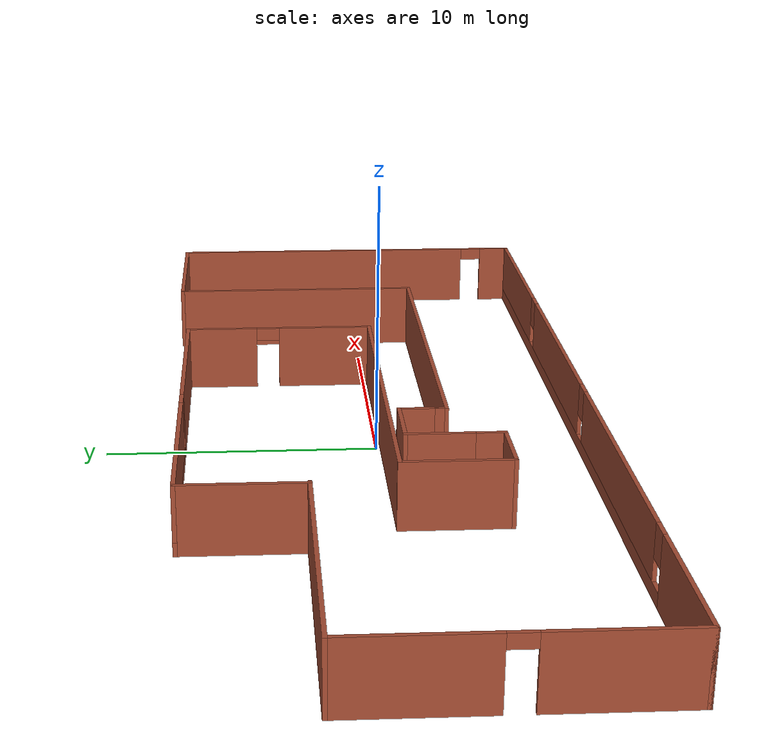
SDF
<?xml version='1.0'?>
<sdf version='1.6'>
  <model name='apartment_model'>
    <link name='Wall_1'>
      <pose frame=''>-13.3 2.8 0 0 -0 3.14159</pose>
      <self_collide>0</self_collide>
      <kinematic>0</kinematic>
      <visual name='Wall_1_Visual'>
        <pose frame=''>0 0 1.25 0 -0 0</pose>
        <geometry>
          <box>
            <size>10 0.15 2.5</size>
          </box>
        </geometry>
        <material>
          <script>
            <uri>file://media/materials/scripts/gazebo.material</uri>
            <name>Gazebo/Bricks</name>
          </script>
          <ambient>1 1 1 1</ambient>
          <diffuse>1 1 1 1</diffuse>
          <specular>0.2 0.2 0.2 1</specular>
          <emissive>0 0 0 1</emissive>
        </material>
        <cast_shadows>1</cast_shadows>
        <transparency>0</transparency>
      </visual>
      <collision name='Wall_1_Collision'>
        <laser_retro>0</laser_retro>
        <max_contacts>10</max_contacts>
        <pose frame=''>0 0 1.25 0 -0 0</pose>
        <geometry>
          <box>
            <size>10 0.15 2.5</size>
          </box>
        </geometry>
        <surface>
          <friction>
            <ode>
              <mu>1</mu>
              <mu2>1</mu2>
              <fdir1>0 0 0</fdir1>
              <slip1>0</slip1>
              <slip2>0</slip2>
            </ode>
            <torsional>
              <coefficient>1</coefficient>
              <patch_radius>0</patch_radius>
              <surface_radius>0</surface_radius>
              <use_patch_radius>1</use_patch_radius>
              <ode>
                <slip>0</slip>
              </ode>
            </torsional>
          </friction>
          <bounce>
            <restitution_coefficient>0</restitution_coefficient>
            <threshold>1e+06</threshold>
          </bounce>
          <contact>
            <collide_without_contact>0</collide_without_contact>
            <collide_without_contact_bitmask>1</collide_without_contact_bitmask>
            <collide_bitmask>1</collide_bitmask>
            <ode>
              <soft_cfm>0</soft_cfm>
              <soft_erp>0.2</soft_erp>
              <kp>1e+13</kp>
              <kd>1</kd>
              <max_vel>0.01</max_vel>
              <min_depth>0</min_depth>
            </ode>
            <bullet>
              <split_impulse>1</split_impulse>
              <split_impulse_penetration_threshold>-0.01</split_impulse_penetration_threshold>
              <soft_cfm>0</soft_cfm>
              <soft_erp>0.2</soft_erp>
              <kp>1e+13</kp>
              <kd>1</kd>
            </bullet>
          </contact>
        </surface>
      </collision>
    </link>
    <link name='Wall_10'>
      <pose frame=''>-4.575 -3.5 0 0 0 -1.5708</pose>
      <self_collide>0</self_collide>
      <kinematic>0</kinematic>
      <visual name='Wall_10_Visual'>
        <pose frame=''>0 0 1.25 0 -0 0</pose>
        <geometry>
          <box>
            <size>1.25 0.15 2.5</size>
          </box>
        </geometry>
        <material>
          <script>
            <uri>file://media/materials/scripts/gazebo.material</uri>
            <name>Gazebo/Bricks</name>
          </script>
          <ambient>1 1 1 1</ambient>
          <diffuse>1 1 1 1</diffuse>
          <specular>0.2 0.2 0.2 1</specular>
          <emissive>0 0 0 1</emissive>
        </material>
        <cast_shadows>1</cast_shadows>
        <transparency>0</transparency>
      </visual>
      <collision name='Wall_10_Collision'>
        <laser_retro>0</laser_retro>
        <max_contacts>10</max_contacts>
        <pose frame=''>0 0 1.25 0 -0 0</pose>
        <geometry>
          <box>
            <size>1.25 0.15 2.5</size>
          </box>
        </geometry>
        <surface>
          <friction>
            <ode>
              <mu>1</mu>
              <mu2>1</mu2>
              <fdir1>0 0 0</fdir1>
              <slip1>0</slip1>
              <slip2>0</slip2>
            </ode>
            <torsional>
              <coefficient>1</coefficient>
              <patch_radius>0</patch_radius>
              <surface_radius>0</surface_radius>
              <use_patch_radius>1</use_patch_radius>
              <ode>
                <slip>0</slip>
              </ode>
            </torsional>
          </friction>
          <bounce>
            <restitution_coefficient>0</restitution_coefficient>
            <threshold>1e+06</threshold>
          </bounce>
          <contact>
            <collide_without_contact>0</collide_without_contact>
            <collide_without_contact_bitmask>1</collide_without_contact_bitmask>
            <collide_bitmask>1</collide_bitmask>
            <ode>
              <soft_cfm>0</soft_cfm>
              <soft_erp>0.2</soft_erp>
              <kp>1e+13</kp>
              <kd>1</kd>
              <max_vel>0.01</max_vel>
              <min_depth>0</min_depth>
            </ode>
            <bullet>
              <split_impulse>1</split_impulse>
              <split_impulse_penetration_threshold>-0.01</split_impulse_penetration_threshold>
              <soft_cfm>0</soft_cfm>
              <soft_erp>0.2</soft_erp>
              <kp>1e+13</kp>
              <kd>1</kd>
            </bullet>
          </contact>
        </surface>
      </collision>
    </link>
    <link name='Wall_11'>
      <pose frame=''>-5.75 -4.05 0 0 -0 3.14159</pose>
      <self_collide>0</self_collide>
      <kinematic>0</kinematic>
      <visual name='Wall_11_Visual'>
        <pose frame=''>0 0 1.25 0 -0 0</pose>
        <geometry>
          <box>
            <size>2.5 0.15 2.5</size>
          </box>
        </geometry>
        <material>
          <script>
            <uri>file://media/materials/scripts/gazebo.material</uri>
            <name>Gazebo/Bricks</name>
          </script>
          <ambient>1 1 1 1</ambient>
          <diffuse>1 1 1 1</diffuse>
          <specular>0.2 0.2 0.2 1</specular>
          <emissive>0 0 0 1</emissive>
        </material>
        <cast_shadows>1</cast_shadows>
        <transparency>0</transparency>
      </visual>
      <collision name='Wall_11_Collision'>
        <laser_retro>0</laser_retro>
        <max_contacts>10</max_contacts>
        <pose frame=''>0 0 1.25 0 -0 0</pose>
        <geometry>
          <box>
            <size>2.5 0.15 2.5</size>
          </box>
        </geometry>
        <surface>
          <friction>
            <ode>
              <mu>1</mu>
              <mu2>1</mu2>
              <fdir1>0 0 0</fdir1>
              <slip1>0</slip1>
              <slip2>0</slip2>
            </ode>
            <torsional>
              <coefficient>1</coefficient>
              <patch_radius>0</patch_radius>
              <surface_radius>0</surface_radius>
              <use_patch_radius>1</use_patch_radius>
              <ode>
                <slip>0</slip>
              </ode>
            </torsional>
          </friction>
          <bounce>
            <restitution_coefficient>0</restitution_coefficient>
            <threshold>1e+06</threshold>
          </bounce>
          <contact>
            <collide_without_contact>0</collide_without_contact>
            <collide_without_contact_bitmask>1</collide_without_contact_bitmask>
            <collide_bitmask>1</collide_bitmask>
            <ode>
              <soft_cfm>0</soft_cfm>
              <soft_erp>0.2</soft_erp>
              <kp>1e+13</kp>
              <kd>1</kd>
              <max_vel>0.01</max_vel>
              <min_depth>0</min_depth>
            </ode>
            <bullet>
              <split_impulse>1</split_impulse>
              <split_impulse_penetration_threshold>-0.01</split_impulse_penetration_threshold>
              <soft_cfm>0</soft_cfm>
              <soft_erp>0.2</soft_erp>
              <kp>1e+13</kp>
              <kd>1</kd>
            </bullet>
          </contact>
        </surface>
      </collision>
    </link>
    <link name='Wall_14'>
      <pose frame=''>-6.925 -2.125 0 0 -0 1.5708</pose>
      <self_collide>0</self_collide>
      <kinematic>0</kinematic>
      <visual name='Wall_14_Visual'>
        <pose frame=''>0 0 1.25 0 -0 0</pose>
        <geometry>
          <box>
            <size>4 0.15 2.5</size>
          </box>
        </geometry>
        <material>
          <script>
            <uri>file://media/materials/scripts/gazebo.material</uri>
            <name>Gazebo/Bricks</name>
          </script>
          <ambient>1 1 1 1</ambient>
          <diffuse>1 1 1 1</diffuse>
          <specular>0.2 0.2 0.2 1</specular>
          <emissive>0 0 0 1</emissive>
        </material>
        <cast_shadows>1</cast_shadows>
        <transparency>0</transparency>
      </visual>
      <collision name='Wall_14_Collision'>
        <laser_retro>0</laser_retro>
        <max_contacts>10</max_contacts>
        <pose frame=''>0 0 1.25 0 -0 0</pose>
        <geometry>
          <box>
            <size>4 0.15 2.5</size>
          </box>
        </geometry>
        <surface>
          <friction>
            <ode>
              <mu>1</mu>
              <mu2>1</mu2>
              <fdir1>0 0 0</fdir1>
              <slip1>0</slip1>
              <slip2>0</slip2>
            </ode>
            <torsional>
              <coefficient>1</coefficient>
              <patch_radius>0</patch_radius>
              <surface_radius>0</surface_radius>
              <use_patch_radius>1</use_patch_radius>
              <ode>
                <slip>0</slip>
              </ode>
            </torsional>
          </friction>
          <bounce>
            <restitution_coefficient>0</restitution_coefficient>
            <threshold>1e+06</threshold>
          </bounce>
          <contact>
            <collide_without_contact>0</collide_without_contact>
            <collide_without_contact_bitmask>1</collide_without_contact_bitmask>
            <collide_bitmask>1</collide_bitmask>
            <ode>
              <soft_cfm>0</soft_cfm>
              <soft_erp>0.2</soft_erp>
              <kp>1e+13</kp>
              <kd>1</kd>
              <max_vel>0.01</max_vel>
              <min_depth>0</min_depth>
            </ode>
            <bullet>
              <split_impulse>1</split_impulse>
              <split_impulse_penetration_threshold>-0.01</split_impulse_penetration_threshold>
              <soft_cfm>0</soft_cfm>
              <soft_erp>0.2</soft_erp>
              <kp>1e+13</kp>
              <kd>1</kd>
            </bullet>
          </contact>
        </surface>
      </collision>
    </link>
    <link name='Wall_15'>
      <pose frame=''>0 -0.2 0 0 -0 0</pose>
      <self_collide>0</self_collide>
      <kinematic>0</kinematic>
      <visual name='Wall_15_Visual'>
        <pose frame=''>0 0 1.25 0 -0 0</pose>
        <geometry>
          <box>
            <size>14 0.15 2.5</size>
          </box>
        </geometry>
        <material>
          <script>
            <uri>file://media/materials/scripts/gazebo.material</uri>
            <name>Gazebo/Bricks</name>
          </script>
          <ambient>1 1 1 1</ambient>
          <diffuse>1 1 1 1</diffuse>
          <specular>0.2 0.2 0.2 1</specular>
          <emissive>0 0 0 1</emissive>
        </material>
        <cast_shadows>1</cast_shadows>
        <transparency>0</transparency>
      </visual>
      <collision name='Wall_15_Collision'>
        <laser_retro>0</laser_retro>
        <max_contacts>10</max_contacts>
        <pose frame=''>0 0 1.25 0 -0 0</pose>
        <geometry>
          <box>
            <size>14 0.15 2.5</size>
          </box>
        </geometry>
        <surface>
          <friction>
            <ode>
              <mu>1</mu>
              <mu2>1</mu2>
              <fdir1>0 0 0</fdir1>
              <slip1>0</slip1>
              <slip2>0</slip2>
            </ode>
            <torsional>
              <coefficient>1</coefficient>
              <patch_radius>0</patch_radius>
              <surface_radius>0</surface_radius>
              <use_patch_radius>1</use_patch_radius>
              <ode>
                <slip>0</slip>
              </ode>
            </torsional>
          </friction>
          <bounce>
            <restitution_coefficient>0</restitution_coefficient>
            <threshold>1e+06</threshold>
          </bounce>
          <contact>
            <collide_without_contact>0</collide_without_contact>
            <collide_without_contact_bitmask>1</collide_without_contact_bitmask>
            <collide_bitmask>1</collide_bitmask>
            <ode>
              <soft_cfm>0</soft_cfm>
              <soft_erp>0.2</soft_erp>
              <kp>1e+13</kp>
              <kd>1</kd>
              <max_vel>0.01</max_vel>
              <min_depth>0</min_depth>
            </ode>
            <bullet>
              <split_impulse>1</split_impulse>
              <split_impulse_penetration_threshold>-0.01</split_impulse_penetration_threshold>
              <soft_cfm>0</soft_cfm>
              <soft_erp>0.2</soft_erp>
              <kp>1e+13</kp>
              <kd>1</kd>
            </bullet>
          </contact>
        </surface>
      </collision>
    </link>
    <link name='Wall_16'>
      <pose frame=''>6.925 3.475 0 0 -0 1.5708</pose>
      <self_collide>0</self_collide>
      <kinematic>0</kinematic>
      <visual name='Wall_16_Visual_0'>
        <pose frame=''>-1.87856 0 1.25 0 -0 0</pose>
        <geometry>
          <box>
            <size>3.74288 0.15 2.5</size>
          </box>
        </geometry>
        <material>
          <script>
            <uri>file://media/materials/scripts/gazebo.material</uri>
            <name>Gazebo/Bricks</name>
          </script>
          <ambient>1 1 1 1</ambient>
          <diffuse>1 1 1 1</diffuse>
          <specular>0.2 0.2 0.2 1</specular>
          <emissive>0 0 0 1</emissive>
        </material>
        <cast_shadows>1</cast_shadows>
        <transparency>0</transparency>
      </visual>
      <visual name='Wall_16_Visual_1'>
        <pose frame=''>2.32144 0 1.25 0 -0 0</pose>
        <geometry>
          <box>
            <size>2.85712 0.15 2.5</size>
          </box>
        </geometry>
        <material>
          <script>
            <uri>file://media/materials/scripts/gazebo.material</uri>
            <name>Gazebo/Bricks</name>
          </script>
          <ambient>1 1 1 1</ambient>
          <diffuse>1 1 1 1</diffuse>
          <specular>0.2 0.2 0.2 1</specular>
          <emissive>0 0 0 1</emissive>
        </material>
        <cast_shadows>1</cast_shadows>
        <transparency>0</transparency>
      </visual>
      <visual name='Wall_16_Visual_2'>
        <pose frame=''>0.442879 0 2.25 0 -0 0</pose>
        <geometry>
          <box>
            <size>0.9 0.15 0.5</size>
          </box>
        </geometry>
        <material>
          <script>
            <uri>file://media/materials/scripts/gazebo.material</uri>
            <name>Gazebo/Bricks</name>
          </script>
          <ambient>1 1 1 1</ambient>
          <diffuse>1 1 1 1</diffuse>
          <specular>0.2 0.2 0.2 1</specular>
          <emissive>0 0 0 1</emissive>
        </material>
        <cast_shadows>1</cast_shadows>
        <transparency>0</transparency>
      </visual>
      <collision name='Wall_16_Collision_0'>
        <laser_retro>0</laser_retro>
        <max_contacts>10</max_contacts>
        <pose frame=''>-1.87856 0 1.25 0 -0 0</pose>
        <geometry>
          <box>
            <size>3.74288 0.15 2.5</size>
          </box>
        </geometry>
        <surface>
          <friction>
            <ode>
              <mu>1</mu>
              <mu2>1</mu2>
              <fdir1>0 0 0</fdir1>
              <slip1>0</slip1>
              <slip2>0</slip2>
            </ode>
            <torsional>
              <coefficient>1</coefficient>
              <patch_radius>0</patch_radius>
              <surface_radius>0</surface_radius>
              <use_patch_radius>1</use_patch_radius>
              <ode>
                <slip>0</slip>
              </ode>
            </torsional>
          </friction>
          <bounce>
            <restitution_coefficient>0</restitution_coefficient>
            <threshold>1e+06</threshold>
          </bounce>
          <contact>
            <collide_without_contact>0</collide_without_contact>
            <collide_without_contact_bitmask>1</collide_without_contact_bitmask>
            <collide_bitmask>1</collide_bitmask>
            <ode>
              <soft_cfm>0</soft_cfm>
              <soft_erp>0.2</soft_erp>
              <kp>1e+13</kp>
              <kd>1</kd>
              <max_vel>0.01</max_vel>
              <min_depth>0</min_depth>
            </ode>
            <bullet>
              <split_impulse>1</split_impulse>
              <split_impulse_penetration_threshold>-0.01</split_impulse_penetration_threshold>
              <soft_cfm>0</soft_cfm>
              <soft_erp>0.2</soft_erp>
              <kp>1e+13</kp>
              <kd>1</kd>
            </bullet>
          </contact>
        </surface>
      </collision>
      <collision name='Wall_16_Collision_1'>
        <laser_retro>0</laser_retro>
        <max_contacts>10</max_contacts>
        <pose frame=''>2.32144 0 1.25 0 -0 0</pose>
        <geometry>
          <box>
            <size>2.85712 0.15 2.5</size>
          </box>
        </geometry>
        <surface>
          <friction>
            <ode>
              <mu>1</mu>
              <mu2>1</mu2>
              <fdir1>0 0 0</fdir1>
              <slip1>0</slip1>
              <slip2>0</slip2>
            </ode>
            <torsional>
              <coefficient>1</coefficient>
              <patch_radius>0</patch_radius>
              <surface_radius>0</surface_radius>
              <use_patch_radius>1</use_patch_radius>
              <ode>
                <slip>0</slip>
              </ode>
            </torsional>
          </friction>
          <bounce>
            <restitution_coefficient>0</restitution_coefficient>
            <threshold>1e+06</threshold>
          </bounce>
          <contact>
            <collide_without_contact>0</collide_without_contact>
            <collide_without_contact_bitmask>1</collide_without_contact_bitmask>
            <collide_bitmask>1</collide_bitmask>
            <ode>
              <soft_cfm>0</soft_cfm>
              <soft_erp>0.2</soft_erp>
              <kp>1e+13</kp>
              <kd>1</kd>
              <max_vel>0.01</max_vel>
              <min_depth>0</min_depth>
            </ode>
            <bullet>
              <split_impulse>1</split_impulse>
              <split_impulse_penetration_threshold>-0.01</split_impulse_penetration_threshold>
              <soft_cfm>0</soft_cfm>
              <soft_erp>0.2</soft_erp>
              <kp>1e+13</kp>
              <kd>1</kd>
            </bullet>
          </contact>
        </surface>
      </collision>
      <collision name='Wall_16_Collision_2'>
        <laser_retro>0</laser_retro>
        <max_contacts>10</max_contacts>
        <pose frame=''>0.442879 0 2.25 0 -0 0</pose>
        <geometry>
          <box>
            <size>0.9 0.15 0.5</size>
          </box>
        </geometry>
        <surface>
          <friction>
            <ode>
              <mu>1</mu>
              <mu2>1</mu2>
              <fdir1>0 0 0</fdir1>
              <slip1>0</slip1>
              <slip2>0</slip2>
            </ode>
            <torsional>
              <coefficient>1</coefficient>
              <patch_radius>0</patch_radius>
              <surface_radius>0</surface_radius>
              <use_patch_radius>1</use_patch_radius>
              <ode>
                <slip>0</slip>
              </ode>
            </torsional>
          </friction>
          <bounce>
            <restitution_coefficient>0</restitution_coefficient>
            <threshold>1e+06</threshold>
          </bounce>
          <contact>
            <collide_without_contact>0</collide_without_contact>
            <collide_without_contact_bitmask>1</collide_without_contact_bitmask>
            <collide_bitmask>1</collide_bitmask>
            <ode>
              <soft_cfm>0</soft_cfm>
              <soft_erp>0.2</soft_erp>
              <kp>1e+13</kp>
              <kd>1</kd>
              <max_vel>0.01</max_vel>
              <min_depth>0</min_depth>
            </ode>
            <bullet>
              <split_impulse>1</split_impulse>
              <split_impulse_penetration_threshold>-0.01</split_impulse_penetration_threshold>
              <soft_cfm>0</soft_cfm>
              <soft_erp>0.2</soft_erp>
              <kp>1e+13</kp>
              <kd>1</kd>
            </bullet>
          </contact>
        </surface>
      </collision>
    </link>
    <link name='Wall_17'>
      <pose frame=''>-0.75 7.15 0 0 -0 3.14159</pose>
      <self_collide>0</self_collide>
      <kinematic>0</kinematic>
      <visual name='Wall_17_Visual_0'>
        <pose frame=''>-4.03161 0 1.25 0 -0 0</pose>
        <geometry>
          <box>
            <size>7.43678 0.15 2.5</size>
          </box>
        </geometry>
        <material>
          <script>
            <uri>file://media/materials/scripts/gazebo.material</uri>
            <name>Gazebo/Bricks</name>
          </script>
          <ambient>1 1 1 1</ambient>
          <diffuse>1 1 1 1</diffuse>
          <specular>0.2 0.2 0.2 1</specular>
          <emissive>0 0 0 1</emissive>
        </material>
        <cast_shadows>1</cast_shadows>
        <transparency>0</transparency>
      </visual>
      <visual name='Wall_17_Visual_1'>
        <pose frame=''>3.71839 0 0.25 0 -0 0</pose>
        <geometry>
          <box>
            <size>8.06322 0.15 0.5</size>
          </box>
        </geometry>
        <material>
          <script>
            <uri>file://media/materials/scripts/gazebo.material</uri>
            <name>Gazebo/Bricks</name>
          </script>
          <ambient>1 1 1 1</ambient>
          <diffuse>1 1 1 1</diffuse>
          <specular>0.2 0.2 0.2 1</specular>
          <emissive>0 0 0 1</emissive>
        </material>
        <cast_shadows>1</cast_shadows>
        <transparency>0</transparency>
      </visual>
      <visual name='Wall_17_Visual_2'>
        <pose frame=''>4.11839 0 1.5 0 -0 0</pose>
        <geometry>
          <box>
            <size>7.26322 0.15 2</size>
          </box>
        </geometry>
        <material>
          <script>
            <uri>file://media/materials/scripts/gazebo.material</uri>
            <name>Gazebo/Bricks</name>
          </script>
          <ambient>1 1 1 1</ambient>
          <diffuse>1 1 1 1</diffuse>
          <specular>0.2 0.2 0.2 1</specular>
          <emissive>0 0 0 1</emissive>
        </material>
        <cast_shadows>1</cast_shadows>
        <transparency>0</transparency>
      </visual>
      <visual name='Wall_17_Visual_3'>
        <pose frame=''>0.086778 0 1.9 0 -0 0</pose>
        <geometry>
          <box>
            <size>0.8 0.15 1.2</size>
          </box>
        </geometry>
        <material>
          <script>
            <uri>file://media/materials/scripts/gazebo.material</uri>
            <name>Gazebo/Bricks</name>
          </script>
          <ambient>1 1 1 1</ambient>
          <diffuse>1 1 1 1</diffuse>
          <specular>0.2 0.2 0.2 1</specular>
          <emissive>0 0 0 1</emissive>
        </material>
        <cast_shadows>1</cast_shadows>
        <transparency>0</transparency>
      </visual>
      <collision name='Wall_17_Collision_0'>
        <laser_retro>0</laser_retro>
        <max_contacts>10</max_contacts>
        <pose frame=''>-4.03161 0 1.25 0 -0 0</pose>
        <geometry>
          <box>
            <size>7.43678 0.15 2.5</size>
          </box>
        </geometry>
        <surface>
          <friction>
            <ode>
              <mu>1</mu>
              <mu2>1</mu2>
              <fdir1>0 0 0</fdir1>
              <slip1>0</slip1>
              <slip2>0</slip2>
            </ode>
            <torsional>
              <coefficient>1</coefficient>
              <patch_radius>0</patch_radius>
              <surface_radius>0</surface_radius>
              <use_patch_radius>1</use_patch_radius>
              <ode>
                <slip>0</slip>
              </ode>
            </torsional>
          </friction>
          <bounce>
            <restitution_coefficient>0</restitution_coefficient>
            <threshold>1e+06</threshold>
          </bounce>
          <contact>
            <collide_without_contact>0</collide_without_contact>
            <collide_without_contact_bitmask>1</collide_without_contact_bitmask>
            <collide_bitmask>1</collide_bitmask>
            <ode>
              <soft_cfm>0</soft_cfm>
              <soft_erp>0.2</soft_erp>
              <kp>1e+13</kp>
              <kd>1</kd>
              <max_vel>0.01</max_vel>
              <min_depth>0</min_depth>
            </ode>
            <bullet>
              <split_impulse>1</split_impulse>
              <split_impulse_penetration_threshold>-0.01</split_impulse_penetration_threshold>
              <soft_cfm>0</soft_cfm>
              <soft_erp>0.2</soft_erp>
              <kp>1e+13</kp>
              <kd>1</kd>
            </bullet>
          </contact>
        </surface>
      </collision>
      <collision name='Wall_17_Collision_1'>
        <laser_retro>0</laser_retro>
        <max_contacts>10</max_contacts>
        <pose frame=''>3.71839 0 0.25 0 -0 0</pose>
        <geometry>
          <box>
            <size>8.06322 0.15 0.5</size>
          </box>
        </geometry>
        <surface>
          <friction>
            <ode>
              <mu>1</mu>
              <mu2>1</mu2>
              <fdir1>0 0 0</fdir1>
              <slip1>0</slip1>
              <slip2>0</slip2>
            </ode>
            <torsional>
              <coefficient>1</coefficient>
              <patch_radius>0</patch_radius>
              <surface_radius>0</surface_radius>
              <use_patch_radius>1</use_patch_radius>
              <ode>
                <slip>0</slip>
              </ode>
            </torsional>
          </friction>
          <bounce>
            <restitution_coefficient>0</restitution_coefficient>
            <threshold>1e+06</threshold>
          </bounce>
          <contact>
            <collide_without_contact>0</collide_without_contact>
            <collide_without_contact_bitmask>1</collide_without_contact_bitmask>
            <collide_bitmask>1</collide_bitmask>
            <ode>
              <soft_cfm>0</soft_cfm>
              <soft_erp>0.2</soft_erp>
              <kp>1e+13</kp>
              <kd>1</kd>
              <max_vel>0.01</max_vel>
              <min_depth>0</min_depth>
            </ode>
            <bullet>
              <split_impulse>1</split_impulse>
              <split_impulse_penetration_threshold>-0.01</split_impulse_penetration_threshold>
              <soft_cfm>0</soft_cfm>
              <soft_erp>0.2</soft_erp>
              <kp>1e+13</kp>
              <kd>1</kd>
            </bullet>
          </contact>
        </surface>
      </collision>
      <collision name='Wall_17_Collision_2'>
        <laser_retro>0</laser_retro>
        <max_contacts>10</max_contacts>
        <pose frame=''>4.11839 0 1.5 0 -0 0</pose>
        <geometry>
          <box>
            <size>7.26322 0.15 2</size>
          </box>
        </geometry>
        <surface>
          <friction>
            <ode>
              <mu>1</mu>
              <mu2>1</mu2>
              <fdir1>0 0 0</fdir1>
              <slip1>0</slip1>
              <slip2>0</slip2>
            </ode>
            <torsional>
              <coefficient>1</coefficient>
              <patch_radius>0</patch_radius>
              <surface_radius>0</surface_radius>
              <use_patch_radius>1</use_patch_radius>
              <ode>
                <slip>0</slip>
              </ode>
            </torsional>
          </friction>
          <bounce>
            <restitution_coefficient>0</restitution_coefficient>
            <threshold>1e+06</threshold>
          </bounce>
          <contact>
            <collide_without_contact>0</collide_without_contact>
            <collide_without_contact_bitmask>1</collide_without_contact_bitmask>
            <collide_bitmask>1</collide_bitmask>
            <ode>
              <soft_cfm>0</soft_cfm>
              <soft_erp>0.2</soft_erp>
              <kp>1e+13</kp>
              <kd>1</kd>
              <max_vel>0.01</max_vel>
              <min_depth>0</min_depth>
            </ode>
            <bullet>
              <split_impulse>1</split_impulse>
              <split_impulse_penetration_threshold>-0.01</split_impulse_penetration_threshold>
              <soft_cfm>0</soft_cfm>
              <soft_erp>0.2</soft_erp>
              <kp>1e+13</kp>
              <kd>1</kd>
            </bullet>
          </contact>
        </surface>
      </collision>
      <collision name='Wall_17_Collision_3'>
        <laser_retro>0</laser_retro>
        <max_contacts>10</max_contacts>
        <pose frame=''>0.086778 0 1.9 0 -0 0</pose>
        <geometry>
          <box>
            <size>0.8 0.15 1.2</size>
          </box>
        </geometry>
        <surface>
          <friction>
            <ode>
              <mu>1</mu>
              <mu2>1</mu2>
              <fdir1>0 0 0</fdir1>
              <slip1>0</slip1>
              <slip2>0</slip2>
            </ode>
            <torsional>
              <coefficient>1</coefficient>
              <patch_radius>0</patch_radius>
              <surface_radius>0</surface_radius>
              <use_patch_radius>1</use_patch_radius>
              <ode>
                <slip>0</slip>
              </ode>
            </torsional>
          </friction>
          <bounce>
            <restitution_coefficient>0</restitution_coefficient>
            <threshold>1e+06</threshold>
          </bounce>
          <contact>
            <collide_without_contact>0</collide_without_contact>
            <collide_without_contact_bitmask>1</collide_without_contact_bitmask>
            <collide_bitmask>1</collide_bitmask>
            <ode>
              <soft_cfm>0</soft_cfm>
              <soft_erp>0.2</soft_erp>
              <kp>1e+13</kp>
              <kd>1</kd>
              <max_vel>0.01</max_vel>
              <min_depth>0</min_depth>
            </ode>
            <bullet>
              <split_impulse>1</split_impulse>
              <split_impulse_penetration_threshold>-0.01</split_impulse_penetration_threshold>
              <soft_cfm>0</soft_cfm>
              <soft_erp>0.2</soft_erp>
              <kp>1e+13</kp>
              <kd>1</kd>
            </bullet>
          </contact>
        </surface>
      </collision>
    </link>
    <link name='Wall_18'>
      <pose frame=''>-8.425 4.975 0 0 0 -1.5708</pose>
      <self_collide>0</self_collide>
      <kinematic>0</kinematic>
      <visual name='Wall_18_Visual'>
        <pose frame=''>0 0 1.25 0 -0 0</pose>
        <geometry>
          <box>
            <size>4.5 0.15 2.5</size>
          </box>
        </geometry>
        <material>
          <script>
            <uri>file://media/materials/scripts/gazebo.material</uri>
            <name>Gazebo/Bricks</name>
          </script>
          <ambient>1 1 1 1</ambient>
          <diffuse>1 1 1 1</diffuse>
          <specular>0.2 0.2 0.2 1</specular>
          <emissive>0 0 0 1</emissive>
        </material>
        <cast_shadows>1</cast_shadows>
        <transparency>0</transparency>
      </visual>
      <collision name='Wall_18_Collision'>
        <laser_retro>0</laser_retro>
        <max_contacts>10</max_contacts>
        <pose frame=''>0 0 1.25 0 -0 0</pose>
        <geometry>
          <box>
            <size>4.5 0.15 2.5</size>
          </box>
        </geometry>
        <surface>
          <friction>
            <ode>
              <mu>1</mu>
              <mu2>1</mu2>
              <fdir1>0 0 0</fdir1>
              <slip1>0</slip1>
              <slip2>0</slip2>
            </ode>
            <torsional>
              <coefficient>1</coefficient>
              <patch_radius>0</patch_radius>
              <surface_radius>0</surface_radius>
              <use_patch_radius>1</use_patch_radius>
              <ode>
                <slip>0</slip>
              </ode>
            </torsional>
          </friction>
          <bounce>
            <restitution_coefficient>0</restitution_coefficient>
            <threshold>1e+06</threshold>
          </bounce>
          <contact>
            <collide_without_contact>0</collide_without_contact>
            <collide_without_contact_bitmask>1</collide_without_contact_bitmask>
            <collide_bitmask>1</collide_bitmask>
            <ode>
              <soft_cfm>0</soft_cfm>
              <soft_erp>0.2</soft_erp>
              <kp>1e+13</kp>
              <kd>1</kd>
              <max_vel>0.01</max_vel>
              <min_depth>0</min_depth>
            </ode>
            <bullet>
              <split_impulse>1</split_impulse>
              <split_impulse_penetration_threshold>-0.01</split_impulse_penetration_threshold>
              <soft_cfm>0</soft_cfm>
              <soft_erp>0.2</soft_erp>
              <kp>1e+13</kp>
              <kd>1</kd>
            </bullet>
          </contact>
        </surface>
      </collision>
    </link>
    <link name='Wall_21'>
      <pose frame=''>18.225 0 0 0 -0 1.5708</pose>
      <self_collide>0</self_collide>
      <kinematic>0</kinematic>
      <visual name='Wall_21_Visual_0'>
        <pose frame=''>-6.96408 0 1.25 0 -0 0</pose>
        <geometry>
          <box>
            <size>1.32185 0.15 2.5</size>
          </box>
        </geometry>
        <material>
          <script>
            <uri>file://media/materials/scripts/gazebo.material</uri>
            <name>Gazebo/Bricks</name>
          </script>
          <ambient>1 1 1 1</ambient>
          <diffuse>1 1 1 1</diffuse>
          <specular>0.2 0.2 0.2 1</specular>
          <emissive>0 0 0 1</emissive>
        </material>
        <cast_shadows>1</cast_shadows>
        <transparency>0</transparency>
      </visual>
      <visual name='Wall_21_Visual_2'>
        <pose frame=''>-5.85315 0 2.25 0 -0 0</pose>
        <geometry>
          <box>
            <size>0.9 0.15 0.5</size>
          </box>
        </geometry>
        <material>
          <script>
            <uri>file://media/materials/scripts/gazebo.material</uri>
            <name>Gazebo/Bricks</name>
          </script>
          <ambient>1 1 1 1</ambient>
          <diffuse>1 1 1 1</diffuse>
          <specular>0.2 0.2 0.2 1</specular>
          <emissive>0 0 0 1</emissive>
        </material>
        <cast_shadows>1</cast_shadows>
        <transparency>0</transparency>
      </visual>
      <visual name='Wall_21_Visual_1'>
        <pose frame=''>1.11092 0 1.25 0 -0 0</pose>
        <geometry>
          <box>
            <size>13.0282 0.15 2.5</size>
          </box>
        </geometry>
        <material>
          <script>
            <uri>file://media/materials/scripts/gazebo.material</uri>
            <name>Gazebo/Bricks</name>
          </script>
          <ambient>1 1 1 1</ambient>
          <diffuse>1 1 1 1</diffuse>
          <specular>0.2 0.2 0.2 1</specular>
          <emissive>0 0 0 1</emissive>
        </material>
        <cast_shadows>1</cast_shadows>
        <transparency>0</transparency>
      </visual>
      <collision name='Wall_21_Collision_0'>
        <laser_retro>0</laser_retro>
        <max_contacts>10</max_contacts>
        <pose frame=''>-6.96408 0 1.25 0 -0 0</pose>
        <geometry>
          <box>
            <size>1.32185 0.15 2.5</size>
          </box>
        </geometry>
        <surface>
          <friction>
            <ode>
              <mu>1</mu>
              <mu2>1</mu2>
              <fdir1>0 0 0</fdir1>
              <slip1>0</slip1>
              <slip2>0</slip2>
            </ode>
            <torsional>
              <coefficient>1</coefficient>
              <patch_radius>0</patch_radius>
              <surface_radius>0</surface_radius>
              <use_patch_radius>1</use_patch_radius>
              <ode>
                <slip>0</slip>
              </ode>
            </torsional>
          </friction>
          <bounce>
            <restitution_coefficient>0</restitution_coefficient>
            <threshold>1e+06</threshold>
          </bounce>
          <contact>
            <collide_without_contact>0</collide_without_contact>
            <collide_without_contact_bitmask>1</collide_without_contact_bitmask>
            <collide_bitmask>1</collide_bitmask>
            <ode>
              <soft_cfm>0</soft_cfm>
              <soft_erp>0.2</soft_erp>
              <kp>1e+13</kp>
              <kd>1</kd>
              <max_vel>0.01</max_vel>
              <min_depth>0</min_depth>
            </ode>
            <bullet>
              <split_impulse>1</split_impulse>
              <split_impulse_penetration_threshold>-0.01</split_impulse_penetration_threshold>
              <soft_cfm>0</soft_cfm>
              <soft_erp>0.2</soft_erp>
              <kp>1e+13</kp>
              <kd>1</kd>
            </bullet>
          </contact>
        </surface>
      </collision>
      <collision name='Wall_21_Collision_1'>
        <laser_retro>0</laser_retro>
        <max_contacts>10</max_contacts>
        <pose frame=''>1.11092 0 1.25 0 -0 0</pose>
        <geometry>
          <box>
            <size>13.0282 0.15 2.5</size>
          </box>
        </geometry>
        <surface>
          <friction>
            <ode>
              <mu>1</mu>
              <mu2>1</mu2>
              <fdir1>0 0 0</fdir1>
              <slip1>0</slip1>
              <slip2>0</slip2>
            </ode>
            <torsional>
              <coefficient>1</coefficient>
              <patch_radius>0</patch_radius>
              <surface_radius>0</surface_radius>
              <use_patch_radius>1</use_patch_radius>
              <ode>
                <slip>0</slip>
              </ode>
            </torsional>
          </friction>
          <bounce>
            <restitution_coefficient>0</restitution_coefficient>
            <threshold>1e+06</threshold>
          </bounce>
          <contact>
            <collide_without_contact>0</collide_without_contact>
            <collide_without_contact_bitmask>1</collide_without_contact_bitmask>
            <collide_bitmask>1</collide_bitmask>
            <ode>
              <soft_cfm>0</soft_cfm>
              <soft_erp>0.2</soft_erp>
              <kp>1e+13</kp>
              <kd>1</kd>
              <max_vel>0.01</max_vel>
              <min_depth>0</min_depth>
            </ode>
            <bullet>
              <split_impulse>1</split_impulse>
              <split_impulse_penetration_threshold>-0.01</split_impulse_penetration_threshold>
              <soft_cfm>0</soft_cfm>
              <soft_erp>0.2</soft_erp>
              <kp>1e+13</kp>
              <kd>1</kd>
            </bullet>
          </contact>
        </surface>
      </collision>
      <collision name='Wall_21_Collision_2'>
        <laser_retro>0</laser_retro>
        <max_contacts>10</max_contacts>
        <pose frame=''>-5.85315 0 2.25 0 -0 0</pose>
        <geometry>
          <box>
            <size>0.9 0.15 0.5</size>
          </box>
        </geometry>
        <surface>
          <friction>
            <ode>
              <mu>1</mu>
              <mu2>1</mu2>
              <fdir1>0 0 0</fdir1>
              <slip1>0</slip1>
              <slip2>0</slip2>
            </ode>
            <torsional>
              <coefficient>1</coefficient>
              <patch_radius>0</patch_radius>
              <surface_radius>0</surface_radius>
              <use_patch_radius>1</use_patch_radius>
              <ode>
                <slip>0</slip>
              </ode>
            </torsional>
          </friction>
          <bounce>
            <restitution_coefficient>0</restitution_coefficient>
            <threshold>1e+06</threshold>
          </bounce>
          <contact>
            <collide_without_contact>0</collide_without_contact>
            <collide_without_contact_bitmask>1</collide_without_contact_bitmask>
            <collide_bitmask>1</collide_bitmask>
            <ode>
              <soft_cfm>0</soft_cfm>
              <soft_erp>0.2</soft_erp>
              <kp>1e+13</kp>
              <kd>1</kd>
              <max_vel>0.01</max_vel>
              <min_depth>0</min_depth>
            </ode>
            <bullet>
              <split_impulse>1</split_impulse>
              <split_impulse_penetration_threshold>-0.01</split_impulse_penetration_threshold>
              <soft_cfm>0</soft_cfm>
              <soft_erp>0.2</soft_erp>
              <kp>1e+13</kp>
              <kd>1</kd>
            </bullet>
          </contact>
        </surface>
      </collision>
    </link>
    <link name='Wall_22'>
      <pose frame=''>15.175 7.55 0 0 -0 3.14159</pose>
      <self_collide>0</self_collide>
      <kinematic>0</kinematic>
      <visual name='Wall_22_Visual'>
        <pose frame=''>0 0 1.25 0 -0 0</pose>
        <geometry>
          <box>
            <size>6.25 0.15 2.5</size>
          </box>
        </geometry>
        <material>
          <script>
            <uri>file://media/materials/scripts/gazebo.material</uri>
            <name>Gazebo/Bricks</name>
          </script>
          <ambient>1 1 1 1</ambient>
          <diffuse>1 1 1 1</diffuse>
          <specular>0.2 0.2 0.2 1</specular>
          <emissive>0 0 0 1</emissive>
        </material>
        <cast_shadows>1</cast_shadows>
        <transparency>0</transparency>
      </visual>
      <collision name='Wall_22_Collision'>
        <laser_retro>0</laser_retro>
        <max_contacts>10</max_contacts>
        <pose frame=''>0 0 1.25 0 -0 0</pose>
        <geometry>
          <box>
            <size>6.25 0.15 2.5</size>
          </box>
        </geometry>
        <surface>
          <friction>
            <ode>
              <mu>1</mu>
              <mu2>1</mu2>
              <fdir1>0 0 0</fdir1>
              <slip1>0</slip1>
              <slip2>0</slip2>
            </ode>
            <torsional>
              <coefficient>1</coefficient>
              <patch_radius>0</patch_radius>
              <surface_radius>0</surface_radius>
              <use_patch_radius>1</use_patch_radius>
              <ode>
                <slip>0</slip>
              </ode>
            </torsional>
          </friction>
          <bounce>
            <restitution_coefficient>0</restitution_coefficient>
            <threshold>1e+06</threshold>
          </bounce>
          <contact>
            <collide_without_contact>0</collide_without_contact>
            <collide_without_contact_bitmask>1</collide_without_contact_bitmask>
            <collide_bitmask>1</collide_bitmask>
            <ode>
              <soft_cfm>0</soft_cfm>
              <soft_erp>0.2</soft_erp>
              <kp>1e+13</kp>
              <kd>1</kd>
              <max_vel>0.01</max_vel>
              <min_depth>0</min_depth>
            </ode>
            <bullet>
              <split_impulse>1</split_impulse>
              <split_impulse_penetration_threshold>-0.01</split_impulse_penetration_threshold>
              <soft_cfm>0</soft_cfm>
              <soft_erp>0.2</soft_erp>
              <kp>1e+13</kp>
              <kd>1</kd>
            </bullet>
          </contact>
        </surface>
      </collision>
    </link>
    <link name='Wall_25'>
      <pose frame=''>12.125 2.625 0 0 0 -1.5708</pose>
      <self_collide>0</self_collide>
      <kinematic>0</kinematic>
      <visual name='Wall_25_Visual'>
        <pose frame=''>0 0 1.25 0 -0 0</pose>
        <geometry>
          <box>
            <size>10 0.15 2.5</size>
          </box>
        </geometry>
        <material>
          <script>
            <uri>file://media/materials/scripts/gazebo.material</uri>
            <name>Gazebo/Bricks</name>
          </script>
          <ambient>1 1 1 1</ambient>
          <diffuse>1 1 1 1</diffuse>
          <specular>0.2 0.2 0.2 1</specular>
          <emissive>0 0 0 1</emissive>
        </material>
        <cast_shadows>1</cast_shadows>
        <transparency>0</transparency>
      </visual>
      <collision name='Wall_25_Collision'>
        <laser_retro>0</laser_retro>
        <max_contacts>10</max_contacts>
        <pose frame=''>0 0 1.25 0 -0 0</pose>
        <geometry>
          <box>
            <size>10 0.15 2.5</size>
          </box>
        </geometry>
        <surface>
          <friction>
            <ode>
              <mu>1</mu>
              <mu2>1</mu2>
              <fdir1>0 0 0</fdir1>
              <slip1>0</slip1>
              <slip2>0</slip2>
            </ode>
            <torsional>
              <coefficient>1</coefficient>
              <patch_radius>0</patch_radius>
              <surface_radius>0</surface_radius>
              <use_patch_radius>1</use_patch_radius>
              <ode>
                <slip>0</slip>
              </ode>
            </torsional>
          </friction>
          <bounce>
            <restitution_coefficient>0</restitution_coefficient>
            <threshold>1e+06</threshold>
          </bounce>
          <contact>
            <collide_without_contact>0</collide_without_contact>
            <collide_without_contact_bitmask>1</collide_without_contact_bitmask>
            <collide_bitmask>1</collide_bitmask>
            <ode>
              <soft_cfm>0</soft_cfm>
              <soft_erp>0.2</soft_erp>
              <kp>1e+13</kp>
              <kd>1</kd>
              <max_vel>0.01</max_vel>
              <min_depth>0</min_depth>
            </ode>
            <bullet>
              <split_impulse>1</split_impulse>
              <split_impulse_penetration_threshold>-0.01</split_impulse_penetration_threshold>
              <soft_cfm>0</soft_cfm>
              <soft_erp>0.2</soft_erp>
              <kp>1e+13</kp>
              <kd>1</kd>
            </bullet>
          </contact>
        </surface>
      </collision>
    </link>
    <link name='Wall_26'>
      <pose frame=''>4.95 -2.3 0 0 -0 3.14159</pose>
      <self_collide>0</self_collide>
      <kinematic>0</kinematic>
      <visual name='Wall_26_Visual'>
        <pose frame=''>0 0 1.25 0 -0 0</pose>
        <geometry>
          <box>
            <size>14.5 0.15 2.5</size>
          </box>
        </geometry>
        <material>
          <script>
            <uri>file://media/materials/scripts/gazebo.material</uri>
            <name>Gazebo/Bricks</name>
          </script>
          <ambient>1 1 1 1</ambient>
          <diffuse>1 1 1 1</diffuse>
          <specular>0.2 0.2 0.2 1</specular>
          <emissive>0 0 0 1</emissive>
        </material>
        <cast_shadows>1</cast_shadows>
        <transparency>0</transparency>
      </visual>
      <collision name='Wall_26_Collision'>
        <laser_retro>0</laser_retro>
        <max_contacts>10</max_contacts>
        <pose frame=''>0 0 1.25 0 -0 0</pose>
        <geometry>
          <box>
            <size>14.5 0.15 2.5</size>
          </box>
        </geometry>
        <surface>
          <friction>
            <ode>
              <mu>1</mu>
              <mu2>1</mu2>
              <fdir1>0 0 0</fdir1>
              <slip1>0</slip1>
              <slip2>0</slip2>
            </ode>
            <torsional>
              <coefficient>1</coefficient>
              <patch_radius>0</patch_radius>
              <surface_radius>0</surface_radius>
              <use_patch_radius>1</use_patch_radius>
              <ode>
                <slip>0</slip>
              </ode>
            </torsional>
          </friction>
          <bounce>
            <restitution_coefficient>0</restitution_coefficient>
            <threshold>1e+06</threshold>
          </bounce>
          <contact>
            <collide_without_contact>0</collide_without_contact>
            <collide_without_contact_bitmask>1</collide_without_contact_bitmask>
            <collide_bitmask>1</collide_bitmask>
            <ode>
              <soft_cfm>0</soft_cfm>
              <soft_erp>0.2</soft_erp>
              <kp>1e+13</kp>
              <kd>1</kd>
              <max_vel>0.01</max_vel>
              <min_depth>0</min_depth>
            </ode>
            <bullet>
              <split_impulse>1</split_impulse>
              <split_impulse_penetration_threshold>-0.01</split_impulse_penetration_threshold>
              <soft_cfm>0</soft_cfm>
              <soft_erp>0.2</soft_erp>
              <kp>1e+13</kp>
              <kd>1</kd>
            </bullet>
          </contact>
        </surface>
      </collision>
    </link>
    <link name='Wall_27'>
      <pose frame=''>-2.225 -2.125 0 0 -0 1.5708</pose>
      <self_collide>0</self_collide>
      <kinematic>0</kinematic>
      <visual name='Wall_27_Visual'>
        <pose frame=''>0 0 1.25 0 -0 0</pose>
        <geometry>
          <box>
            <size>0.5 0.15 2.5</size>
          </box>
        </geometry>
        <material>
          <script>
            <uri>file://media/materials/scripts/gazebo.material</uri>
            <name>Gazebo/Bricks</name>
          </script>
          <ambient>1 1 1 1</ambient>
          <diffuse>1 1 1 1</diffuse>
          <specular>0.2 0.2 0.2 1</specular>
          <emissive>0 0 0 1</emissive>
        </material>
        <cast_shadows>1</cast_shadows>
        <transparency>0</transparency>
      </visual>
      <collision name='Wall_27_Collision'>
        <laser_retro>0</laser_retro>
        <max_contacts>10</max_contacts>
        <pose frame=''>0 0 1.25 0 -0 0</pose>
        <geometry>
          <box>
            <size>0.5 0.15 2.5</size>
          </box>
        </geometry>
        <surface>
          <friction>
            <ode>
              <mu>1</mu>
              <mu2>1</mu2>
              <fdir1>0 0 0</fdir1>
              <slip1>0</slip1>
              <slip2>0</slip2>
            </ode>
            <torsional>
              <coefficient>1</coefficient>
              <patch_radius>0</patch_radius>
              <surface_radius>0</surface_radius>
              <use_patch_radius>1</use_patch_radius>
              <ode>
                <slip>0</slip>
              </ode>
            </torsional>
          </friction>
          <bounce>
            <restitution_coefficient>0</restitution_coefficient>
            <threshold>1e+06</threshold>
          </bounce>
          <contact>
            <collide_without_contact>0</collide_without_contact>
            <collide_without_contact_bitmask>1</collide_without_contact_bitmask>
            <collide_bitmask>1</collide_bitmask>
            <ode>
              <soft_cfm>0</soft_cfm>
              <soft_erp>0.2</soft_erp>
              <kp>1e+13</kp>
              <kd>1</kd>
              <max_vel>0.01</max_vel>
              <min_depth>0</min_depth>
            </ode>
            <bullet>
              <split_impulse>1</split_impulse>
              <split_impulse_penetration_threshold>-0.01</split_impulse_penetration_threshold>
              <soft_cfm>0</soft_cfm>
              <soft_erp>0.2</soft_erp>
              <kp>1e+13</kp>
              <kd>1</kd>
            </bullet>
          </contact>
        </surface>
      </collision>
    </link>
    <link name='Wall_29'>
      <pose frame=''>0 -7.55 0 0 -0 0</pose>
      <self_collide>0</self_collide>
      <kinematic>0</kinematic>
      <visual name='Wall_29_Visual_0'>
        <pose frame=''>-15.4905 0 1.25 0 -0 0</pose>
        <geometry>
          <box>
            <size>5.61904 0.15 2.5</size>
          </box>
        </geometry>
        <material>
          <script>
            <uri>file://media/materials/scripts/gazebo.material</uri>
            <name>Gazebo/Bricks</name>
          </script>
          <ambient>1 1 1 1</ambient>
          <diffuse>1 1 1 1</diffuse>
          <specular>0.2 0.2 0.2 1</specular>
          <emissive>0 0 0 1</emissive>
        </material>
        <cast_shadows>1</cast_shadows>
        <transparency>0</transparency>
      </visual>
      <visual name='Wall_29_Visual_1'>
        <pose frame=''>2.80952 0 0.25 0 -0 0</pose>
        <geometry>
          <box>
            <size>30.981 0.15 0.5</size>
          </box>
        </geometry>
        <material>
          <script>
            <uri>file://media/materials/scripts/gazebo.material</uri>
            <name>Gazebo/Bricks</name>
          </script>
          <ambient>1 1 1 1</ambient>
          <diffuse>1 1 1 1</diffuse>
          <specular>0.2 0.2 0.2 1</specular>
          <emissive>0 0 0 1</emissive>
        </material>
        <cast_shadows>1</cast_shadows>
        <transparency>0</transparency>
      </visual>
      <visual name='Wall_29_Visual_3'>
        <pose frame=''>4.73149 0 1.5 0 -0 0</pose>
        <geometry>
          <box>
            <size>9.72127 0.15 2</size>
          </box>
        </geometry>
        <material>
          <script>
            <uri>file://media/materials/scripts/gazebo.material</uri>
            <name>Gazebo/Bricks</name>
          </script>
          <ambient>1 1 1 1</ambient>
          <diffuse>1 1 1 1</diffuse>
          <specular>0.2 0.2 0.2 1</specular>
          <emissive>0 0 0 1</emissive>
        </material>
        <cast_shadows>1</cast_shadows>
        <transparency>0</transparency>
      </visual>
      <visual name='Wall_29_Visual_2'>
        <pose frame=''>-6.40505 0 1.5 0 -0 0</pose>
        <geometry>
          <box>
            <size>10.9518 0.15 2</size>
          </box>
        </geometry>
        <material>
          <script>
            <uri>file://media/materials/scripts/gazebo.material</uri>
            <name>Gazebo/Bricks</name>
          </script>
          <ambient>1 1 1 1</ambient>
          <diffuse>1 1 1 1</diffuse>
          <specular>0.2 0.2 0.2 1</specular>
          <emissive>0 0 0 1</emissive>
        </material>
        <cast_shadows>1</cast_shadows>
        <transparency>0</transparency>
      </visual>
      <visual name='Wall_29_Visual_4'>
        <pose frame=''>14.3461 0 1.5 0 -0 0</pose>
        <geometry>
          <box>
            <size>7.90787 0.15 2</size>
          </box>
        </geometry>
        <material>
          <script>
            <uri>file://media/materials/scripts/gazebo.material</uri>
            <name>Gazebo/Bricks</name>
          </script>
          <ambient>1 1 1 1</ambient>
          <diffuse>1 1 1 1</diffuse>
          <specular>0.2 0.2 0.2 1</specular>
          <emissive>0 0 0 1</emissive>
        </material>
        <cast_shadows>1</cast_shadows>
        <transparency>0</transparency>
      </visual>
      <visual name='Wall_29_Visual_5'>
        <pose frame=''>-12.281 0 1.9 0 -0 0</pose>
        <geometry>
          <box>
            <size>0.8 0.15 1.2</size>
          </box>
        </geometry>
        <material>
          <script>
            <uri>file://media/materials/scripts/gazebo.material</uri>
            <name>Gazebo/Bricks</name>
          </script>
          <ambient>1 1 1 1</ambient>
          <diffuse>1 1 1 1</diffuse>
          <specular>0.2 0.2 0.2 1</specular>
          <emissive>0 0 0 1</emissive>
        </material>
        <cast_shadows>1</cast_shadows>
        <transparency>0</transparency>
      </visual>
      <visual name='Wall_29_Visual_6'>
        <pose frame=''>-0.529139 0 1.9 0 -0 0</pose>
        <geometry>
          <box>
            <size>0.8 0.15 1.2</size>
          </box>
        </geometry>
        <material>
          <script>
            <uri>file://media/materials/scripts/gazebo.material</uri>
            <name>Gazebo/Bricks</name>
          </script>
          <ambient>1 1 1 1</ambient>
          <diffuse>1 1 1 1</diffuse>
          <specular>0.2 0.2 0.2 1</specular>
          <emissive>0 0 0 1</emissive>
        </material>
        <cast_shadows>1</cast_shadows>
        <transparency>0</transparency>
      </visual>
      <visual name='Wall_29_Visual_7'>
        <pose frame=''>9.99213 0 1.9 0 -0 0</pose>
        <geometry>
          <box>
            <size>0.8 0.15 1.2</size>
          </box>
        </geometry>
        <material>
          <script>
            <uri>file://media/materials/scripts/gazebo.material</uri>
            <name>Gazebo/Bricks</name>
          </script>
          <ambient>1 1 1 1</ambient>
          <diffuse>1 1 1 1</diffuse>
          <specular>0.2 0.2 0.2 1</specular>
          <emissive>0 0 0 1</emissive>
        </material>
        <cast_shadows>1</cast_shadows>
        <transparency>0</transparency>
      </visual>
      <collision name='Wall_29_Collision_0'>
        <laser_retro>0</laser_retro>
        <max_contacts>10</max_contacts>
        <pose frame=''>-15.4905 0 1.25 0 -0 0</pose>
        <geometry>
          <box>
            <size>5.61904 0.15 2.5</size>
          </box>
        </geometry>
        <surface>
          <friction>
            <ode>
              <mu>1</mu>
              <mu2>1</mu2>
              <fdir1>0 0 0</fdir1>
              <slip1>0</slip1>
              <slip2>0</slip2>
            </ode>
            <torsional>
              <coefficient>1</coefficient>
              <patch_radius>0</patch_radius>
              <surface_radius>0</surface_radius>
              <use_patch_radius>1</use_patch_radius>
              <ode>
                <slip>0</slip>
              </ode>
            </torsional>
          </friction>
          <bounce>
            <restitution_coefficient>0</restitution_coefficient>
            <threshold>1e+06</threshold>
          </bounce>
          <contact>
            <collide_without_contact>0</collide_without_contact>
            <collide_without_contact_bitmask>1</collide_without_contact_bitmask>
            <collide_bitmask>1</collide_bitmask>
            <ode>
              <soft_cfm>0</soft_cfm>
              <soft_erp>0.2</soft_erp>
              <kp>1e+13</kp>
              <kd>1</kd>
              <max_vel>0.01</max_vel>
              <min_depth>0</min_depth>
            </ode>
            <bullet>
              <split_impulse>1</split_impulse>
              <split_impulse_penetration_threshold>-0.01</split_impulse_penetration_threshold>
              <soft_cfm>0</soft_cfm>
              <soft_erp>0.2</soft_erp>
              <kp>1e+13</kp>
              <kd>1</kd>
            </bullet>
          </contact>
        </surface>
      </collision>
      <collision name='Wall_29_Collision_1'>
        <laser_retro>0</laser_retro>
        <max_contacts>10</max_contacts>
        <pose frame=''>2.80952 0 0.25 0 -0 0</pose>
        <geometry>
          <box>
            <size>30.981 0.15 0.5</size>
          </box>
        </geometry>
        <surface>
          <friction>
            <ode>
              <mu>1</mu>
              <mu2>1</mu2>
              <fdir1>0 0 0</fdir1>
              <slip1>0</slip1>
              <slip2>0</slip2>
            </ode>
            <torsional>
              <coefficient>1</coefficient>
              <patch_radius>0</patch_radius>
              <surface_radius>0</surface_radius>
              <use_patch_radius>1</use_patch_radius>
              <ode>
                <slip>0</slip>
              </ode>
            </torsional>
          </friction>
          <bounce>
            <restitution_coefficient>0</restitution_coefficient>
            <threshold>1e+06</threshold>
          </bounce>
          <contact>
            <collide_without_contact>0</collide_without_contact>
            <collide_without_contact_bitmask>1</collide_without_contact_bitmask>
            <collide_bitmask>1</collide_bitmask>
            <ode>
              <soft_cfm>0</soft_cfm>
              <soft_erp>0.2</soft_erp>
              <kp>1e+13</kp>
              <kd>1</kd>
              <max_vel>0.01</max_vel>
              <min_depth>0</min_depth>
            </ode>
            <bullet>
              <split_impulse>1</split_impulse>
              <split_impulse_penetration_threshold>-0.01</split_impulse_penetration_threshold>
              <soft_cfm>0</soft_cfm>
              <soft_erp>0.2</soft_erp>
              <kp>1e+13</kp>
              <kd>1</kd>
            </bullet>
          </contact>
        </surface>
      </collision>
      <collision name='Wall_29_Collision_2'>
        <laser_retro>0</laser_retro>
        <max_contacts>10</max_contacts>
        <pose frame=''>-6.40505 0 1.5 0 -0 0</pose>
        <geometry>
          <box>
            <size>10.9518 0.15 2</size>
          </box>
        </geometry>
        <surface>
          <friction>
            <ode>
              <mu>1</mu>
              <mu2>1</mu2>
              <fdir1>0 0 0</fdir1>
              <slip1>0</slip1>
              <slip2>0</slip2>
            </ode>
            <torsional>
              <coefficient>1</coefficient>
              <patch_radius>0</patch_radius>
              <surface_radius>0</surface_radius>
              <use_patch_radius>1</use_patch_radius>
              <ode>
                <slip>0</slip>
              </ode>
            </torsional>
          </friction>
          <bounce>
            <restitution_coefficient>0</restitution_coefficient>
            <threshold>1e+06</threshold>
          </bounce>
          <contact>
            <collide_without_contact>0</collide_without_contact>
            <collide_without_contact_bitmask>1</collide_without_contact_bitmask>
            <collide_bitmask>1</collide_bitmask>
            <ode>
              <soft_cfm>0</soft_cfm>
              <soft_erp>0.2</soft_erp>
              <kp>1e+13</kp>
              <kd>1</kd>
              <max_vel>0.01</max_vel>
              <min_depth>0</min_depth>
            </ode>
            <bullet>
              <split_impulse>1</split_impulse>
              <split_impulse_penetration_threshold>-0.01</split_impulse_penetration_threshold>
              <soft_cfm>0</soft_cfm>
              <soft_erp>0.2</soft_erp>
              <kp>1e+13</kp>
              <kd>1</kd>
            </bullet>
          </contact>
        </surface>
      </collision>
      <collision name='Wall_29_Collision_4'>
        <laser_retro>0</laser_retro>
        <max_contacts>10</max_contacts>
        <pose frame=''>14.3461 0 1.5 0 -0 0</pose>
        <geometry>
          <box>
            <size>7.90787 0.15 2</size>
          </box>
        </geometry>
        <surface>
          <friction>
            <ode>
              <mu>1</mu>
              <mu2>1</mu2>
              <fdir1>0 0 0</fdir1>
              <slip1>0</slip1>
              <slip2>0</slip2>
            </ode>
            <torsional>
              <coefficient>1</coefficient>
              <patch_radius>0</patch_radius>
              <surface_radius>0</surface_radius>
              <use_patch_radius>1</use_patch_radius>
              <ode>
                <slip>0</slip>
              </ode>
            </torsional>
          </friction>
          <bounce>
            <restitution_coefficient>0</restitution_coefficient>
            <threshold>1e+06</threshold>
          </bounce>
          <contact>
            <collide_without_contact>0</collide_without_contact>
            <collide_without_contact_bitmask>1</collide_without_contact_bitmask>
            <collide_bitmask>1</collide_bitmask>
            <ode>
              <soft_cfm>0</soft_cfm>
              <soft_erp>0.2</soft_erp>
              <kp>1e+13</kp>
              <kd>1</kd>
              <max_vel>0.01</max_vel>
              <min_depth>0</min_depth>
            </ode>
            <bullet>
              <split_impulse>1</split_impulse>
              <split_impulse_penetration_threshold>-0.01</split_impulse_penetration_threshold>
              <soft_cfm>0</soft_cfm>
              <soft_erp>0.2</soft_erp>
              <kp>1e+13</kp>
              <kd>1</kd>
            </bullet>
          </contact>
        </surface>
      </collision>
      <collision name='Wall_29_Collision_3'>
        <laser_retro>0</laser_retro>
        <max_contacts>10</max_contacts>
        <pose frame=''>4.73149 0 1.5 0 -0 0</pose>
        <geometry>
          <box>
            <size>9.72127 0.15 2</size>
          </box>
        </geometry>
        <surface>
          <friction>
            <ode>
              <mu>1</mu>
              <mu2>1</mu2>
              <fdir1>0 0 0</fdir1>
              <slip1>0</slip1>
              <slip2>0</slip2>
            </ode>
            <torsional>
              <coefficient>1</coefficient>
              <patch_radius>0</patch_radius>
              <surface_radius>0</surface_radius>
              <use_patch_radius>1</use_patch_radius>
              <ode>
                <slip>0</slip>
              </ode>
            </torsional>
          </friction>
          <bounce>
            <restitution_coefficient>0</restitution_coefficient>
            <threshold>1e+06</threshold>
          </bounce>
          <contact>
            <collide_without_contact>0</collide_without_contact>
            <collide_without_contact_bitmask>1</collide_without_contact_bitmask>
            <collide_bitmask>1</collide_bitmask>
            <ode>
              <soft_cfm>0</soft_cfm>
              <soft_erp>0.2</soft_erp>
              <kp>1e+13</kp>
              <kd>1</kd>
              <max_vel>0.01</max_vel>
              <min_depth>0</min_depth>
            </ode>
            <bullet>
              <split_impulse>1</split_impulse>
              <split_impulse_penetration_threshold>-0.01</split_impulse_penetration_threshold>
              <soft_cfm>0</soft_cfm>
              <soft_erp>0.2</soft_erp>
              <kp>1e+13</kp>
              <kd>1</kd>
            </bullet>
          </contact>
        </surface>
      </collision>
      <collision name='Wall_29_Collision_5'>
        <laser_retro>0</laser_retro>
        <max_contacts>10</max_contacts>
        <pose frame=''>-12.281 0 1.9 0 -0 0</pose>
        <geometry>
          <box>
            <size>0.8 0.15 1.2</size>
          </box>
        </geometry>
        <surface>
          <friction>
            <ode>
              <mu>1</mu>
              <mu2>1</mu2>
              <fdir1>0 0 0</fdir1>
              <slip1>0</slip1>
              <slip2>0</slip2>
            </ode>
            <torsional>
              <coefficient>1</coefficient>
              <patch_radius>0</patch_radius>
              <surface_radius>0</surface_radius>
              <use_patch_radius>1</use_patch_radius>
              <ode>
                <slip>0</slip>
              </ode>
            </torsional>
          </friction>
          <bounce>
            <restitution_coefficient>0</restitution_coefficient>
            <threshold>1e+06</threshold>
          </bounce>
          <contact>
            <collide_without_contact>0</collide_without_contact>
            <collide_without_contact_bitmask>1</collide_without_contact_bitmask>
            <collide_bitmask>1</collide_bitmask>
            <ode>
              <soft_cfm>0</soft_cfm>
              <soft_erp>0.2</soft_erp>
              <kp>1e+13</kp>
              <kd>1</kd>
              <max_vel>0.01</max_vel>
              <min_depth>0</min_depth>
            </ode>
            <bullet>
              <split_impulse>1</split_impulse>
              <split_impulse_penetration_threshold>-0.01</split_impulse_penetration_threshold>
              <soft_cfm>0</soft_cfm>
              <soft_erp>0.2</soft_erp>
              <kp>1e+13</kp>
              <kd>1</kd>
            </bullet>
          </contact>
        </surface>
      </collision>
      <collision name='Wall_29_Collision_6'>
        <laser_retro>0</laser_retro>
        <max_contacts>10</max_contacts>
        <pose frame=''>-0.529139 0 1.9 0 -0 0</pose>
        <geometry>
          <box>
            <size>0.8 0.15 1.2</size>
          </box>
        </geometry>
        <surface>
          <friction>
            <ode>
              <mu>1</mu>
              <mu2>1</mu2>
              <fdir1>0 0 0</fdir1>
              <slip1>0</slip1>
              <slip2>0</slip2>
            </ode>
            <torsional>
              <coefficient>1</coefficient>
              <patch_radius>0</patch_radius>
              <surface_radius>0</surface_radius>
              <use_patch_radius>1</use_patch_radius>
              <ode>
                <slip>0</slip>
              </ode>
            </torsional>
          </friction>
          <bounce>
            <restitution_coefficient>0</restitution_coefficient>
            <threshold>1e+06</threshold>
          </bounce>
          <contact>
            <collide_without_contact>0</collide_without_contact>
            <collide_without_contact_bitmask>1</collide_without_contact_bitmask>
            <collide_bitmask>1</collide_bitmask>
            <ode>
              <soft_cfm>0</soft_cfm>
              <soft_erp>0.2</soft_erp>
              <kp>1e+13</kp>
              <kd>1</kd>
              <max_vel>0.01</max_vel>
              <min_depth>0</min_depth>
            </ode>
            <bullet>
              <split_impulse>1</split_impulse>
              <split_impulse_penetration_threshold>-0.01</split_impulse_penetration_threshold>
              <soft_cfm>0</soft_cfm>
              <soft_erp>0.2</soft_erp>
              <kp>1e+13</kp>
              <kd>1</kd>
            </bullet>
          </contact>
        </surface>
      </collision>
      <collision name='Wall_29_Collision_7'>
        <laser_retro>0</laser_retro>
        <max_contacts>10</max_contacts>
        <pose frame=''>9.99213 0 1.9 0 -0 0</pose>
        <geometry>
          <box>
            <size>0.8 0.15 1.2</size>
          </box>
        </geometry>
        <surface>
          <friction>
            <ode>
              <mu>1</mu>
              <mu2>1</mu2>
              <fdir1>0 0 0</fdir1>
              <slip1>0</slip1>
              <slip2>0</slip2>
            </ode>
            <torsional>
              <coefficient>1</coefficient>
              <patch_radius>0</patch_radius>
              <surface_radius>0</surface_radius>
              <use_patch_radius>1</use_patch_radius>
              <ode>
                <slip>0</slip>
              </ode>
            </torsional>
          </friction>
          <bounce>
            <restitution_coefficient>0</restitution_coefficient>
            <threshold>1e+06</threshold>
          </bounce>
          <contact>
            <collide_without_contact>0</collide_without_contact>
            <collide_without_contact_bitmask>1</collide_without_contact_bitmask>
            <collide_bitmask>1</collide_bitmask>
            <ode>
              <soft_cfm>0</soft_cfm>
              <soft_erp>0.2</soft_erp>
              <kp>1e+13</kp>
              <kd>1</kd>
              <max_vel>0.01</max_vel>
              <min_depth>0</min_depth>
            </ode>
            <bullet>
              <split_impulse>1</split_impulse>
              <split_impulse_penetration_threshold>-0.01</split_impulse_penetration_threshold>
              <soft_cfm>0</soft_cfm>
              <soft_erp>0.2</soft_erp>
              <kp>1e+13</kp>
              <kd>1</kd>
            </bullet>
          </contact>
        </surface>
      </collision>
    </link>
    <link name='Wall_3'>
      <pose frame=''>-18.225 -2.375 0 0 0 -1.5708</pose>
      <self_collide>0</self_collide>
      <kinematic>0</kinematic>
      <visual name='Wall_3_Visual_0'>
        <pose frame=''>-2.83035 0 1.25 0 -0 0</pose>
        <geometry>
          <box>
            <size>4.8393 0.15 2.5</size>
          </box>
        </geometry>
        <material>
          <script>
            <uri>file://media/materials/scripts/gazebo.material</uri>
            <name>Gazebo/Bricks</name>
          </script>
          <ambient>1 1 1 1</ambient>
          <diffuse>1 1 1 1</diffuse>
          <specular>0.2 0.2 0.2 1</specular>
          <emissive>0 0 0 1</emissive>
        </material>
        <cast_shadows>1</cast_shadows>
        <transparency>0</transparency>
      </visual>
      <visual name='Wall_3_Visual_1'>
        <pose frame=''>2.86965 0 1.25 0 -0 0</pose>
        <geometry>
          <box>
            <size>4.7607 0.15 2.5</size>
          </box>
        </geometry>
        <material>
          <script>
            <uri>file://media/materials/scripts/gazebo.material</uri>
            <name>Gazebo/Bricks</name>
          </script>
          <ambient>1 1 1 1</ambient>
          <diffuse>1 1 1 1</diffuse>
          <specular>0.2 0.2 0.2 1</specular>
          <emissive>0 0 0 1</emissive>
        </material>
        <cast_shadows>1</cast_shadows>
        <transparency>0</transparency>
      </visual>
      <visual name='Wall_3_Visual_2'>
        <pose frame=''>0.039298 0 2.25 0 -0 0</pose>
        <geometry>
          <box>
            <size>0.9 0.15 0.5</size>
          </box>
        </geometry>
        <material>
          <script>
            <uri>file://media/materials/scripts/gazebo.material</uri>
            <name>Gazebo/Bricks</name>
          </script>
          <ambient>1 1 1 1</ambient>
          <diffuse>1 1 1 1</diffuse>
          <specular>0.2 0.2 0.2 1</specular>
          <emissive>0 0 0 1</emissive>
        </material>
        <cast_shadows>1</cast_shadows>
        <transparency>0</transparency>
      </visual>
      <collision name='Wall_3_Collision_0'>
        <laser_retro>0</laser_retro>
        <max_contacts>10</max_contacts>
        <pose frame=''>-2.83035 0 1.25 0 -0 0</pose>
        <geometry>
          <box>
            <size>4.8393 0.15 2.5</size>
          </box>
        </geometry>
        <surface>
          <friction>
            <ode>
              <mu>1</mu>
              <mu2>1</mu2>
              <fdir1>0 0 0</fdir1>
              <slip1>0</slip1>
              <slip2>0</slip2>
            </ode>
            <torsional>
              <coefficient>1</coefficient>
              <patch_radius>0</patch_radius>
              <surface_radius>0</surface_radius>
              <use_patch_radius>1</use_patch_radius>
              <ode>
                <slip>0</slip>
              </ode>
            </torsional>
          </friction>
          <bounce>
            <restitution_coefficient>0</restitution_coefficient>
            <threshold>1e+06</threshold>
          </bounce>
          <contact>
            <collide_without_contact>0</collide_without_contact>
            <collide_without_contact_bitmask>1</collide_without_contact_bitmask>
            <collide_bitmask>1</collide_bitmask>
            <ode>
              <soft_cfm>0</soft_cfm>
              <soft_erp>0.2</soft_erp>
              <kp>1e+13</kp>
              <kd>1</kd>
              <max_vel>0.01</max_vel>
              <min_depth>0</min_depth>
            </ode>
            <bullet>
              <split_impulse>1</split_impulse>
              <split_impulse_penetration_threshold>-0.01</split_impulse_penetration_threshold>
              <soft_cfm>0</soft_cfm>
              <soft_erp>0.2</soft_erp>
              <kp>1e+13</kp>
              <kd>1</kd>
            </bullet>
          </contact>
        </surface>
      </collision>
      <collision name='Wall_3_Collision_1'>
        <laser_retro>0</laser_retro>
        <max_contacts>10</max_contacts>
        <pose frame=''>2.86965 0 1.25 0 -0 0</pose>
        <geometry>
          <box>
            <size>4.7607 0.15 2.5</size>
          </box>
        </geometry>
        <surface>
          <friction>
            <ode>
              <mu>1</mu>
              <mu2>1</mu2>
              <fdir1>0 0 0</fdir1>
              <slip1>0</slip1>
              <slip2>0</slip2>
            </ode>
            <torsional>
              <coefficient>1</coefficient>
              <patch_radius>0</patch_radius>
              <surface_radius>0</surface_radius>
              <use_patch_radius>1</use_patch_radius>
              <ode>
                <slip>0</slip>
              </ode>
            </torsional>
          </friction>
          <bounce>
            <restitution_coefficient>0</restitution_coefficient>
            <threshold>1e+06</threshold>
          </bounce>
          <contact>
            <collide_without_contact>0</collide_without_contact>
            <collide_without_contact_bitmask>1</collide_without_contact_bitmask>
            <collide_bitmask>1</collide_bitmask>
            <ode>
              <soft_cfm>0</soft_cfm>
              <soft_erp>0.2</soft_erp>
              <kp>1e+13</kp>
              <kd>1</kd>
              <max_vel>0.01</max_vel>
              <min_depth>0</min_depth>
            </ode>
            <bullet>
              <split_impulse>1</split_impulse>
              <split_impulse_penetration_threshold>-0.01</split_impulse_penetration_threshold>
              <soft_cfm>0</soft_cfm>
              <soft_erp>0.2</soft_erp>
              <kp>1e+13</kp>
              <kd>1</kd>
            </bullet>
          </contact>
        </surface>
      </collision>
      <collision name='Wall_3_Collision_2'>
        <laser_retro>0</laser_retro>
        <max_contacts>10</max_contacts>
        <pose frame=''>0.039298 0 2.25 0 -0 0</pose>
        <geometry>
          <box>
            <size>0.9 0.15 0.5</size>
          </box>
        </geometry>
        <surface>
          <friction>
            <ode>
              <mu>1</mu>
              <mu2>1</mu2>
              <fdir1>0 0 0</fdir1>
              <slip1>0</slip1>
              <slip2>0</slip2>
            </ode>
            <torsional>
              <coefficient>1</coefficient>
              <patch_radius>0</patch_radius>
              <surface_radius>0</surface_radius>
              <use_patch_radius>1</use_patch_radius>
              <ode>
                <slip>0</slip>
              </ode>
            </torsional>
          </friction>
          <bounce>
            <restitution_coefficient>0</restitution_coefficient>
            <threshold>1e+06</threshold>
          </bounce>
          <contact>
            <collide_without_contact>0</collide_without_contact>
            <collide_without_contact_bitmask>1</collide_without_contact_bitmask>
            <collide_bitmask>1</collide_bitmask>
            <ode>
              <soft_cfm>0</soft_cfm>
              <soft_erp>0.2</soft_erp>
              <kp>1e+13</kp>
              <kd>1</kd>
              <max_vel>0.01</max_vel>
              <min_depth>0</min_depth>
            </ode>
            <bullet>
              <split_impulse>1</split_impulse>
              <split_impulse_penetration_threshold>-0.01</split_impulse_penetration_threshold>
              <soft_cfm>0</soft_cfm>
              <soft_erp>0.2</soft_erp>
              <kp>1e+13</kp>
              <kd>1</kd>
            </bullet>
          </contact>
        </surface>
      </collision>
    </link>
    <link name='Wall_7'>
      <pose frame=''>-2.225 -1.275 0 0 -0 1.5708</pose>
      <self_collide>0</self_collide>
      <kinematic>0</kinematic>
      <visual name='Wall_7_Visual'>
        <pose frame=''>0 0 1.25 0 -0 0</pose>
        <geometry>
          <box>
            <size>1.5 0.15 2.5</size>
          </box>
        </geometry>
        <material>
          <script>
            <uri>file://media/materials/scripts/gazebo.material</uri>
            <name>Gazebo/Bricks</name>
          </script>
          <ambient>1 1 1 1</ambient>
          <diffuse>1 1 1 1</diffuse>
          <specular>0.2 0.2 0.2 1</specular>
          <emissive>0 0 0 1</emissive>
        </material>
        <cast_shadows>1</cast_shadows>
        <transparency>0</transparency>
      </visual>
      <collision name='Wall_7_Collision'>
        <laser_retro>0</laser_retro>
        <max_contacts>10</max_contacts>
        <pose frame=''>0 0 1.25 0 -0 0</pose>
        <geometry>
          <box>
            <size>1.5 0.15 2.5</size>
          </box>
        </geometry>
        <surface>
          <friction>
            <ode>
              <mu>1</mu>
              <mu2>1</mu2>
              <fdir1>0 0 0</fdir1>
              <slip1>0</slip1>
              <slip2>0</slip2>
            </ode>
            <torsional>
              <coefficient>1</coefficient>
              <patch_radius>0</patch_radius>
              <surface_radius>0</surface_radius>
              <use_patch_radius>1</use_patch_radius>
              <ode>
                <slip>0</slip>
              </ode>
            </torsional>
          </friction>
          <bounce>
            <restitution_coefficient>0</restitution_coefficient>
            <threshold>1e+06</threshold>
          </bounce>
          <contact>
            <collide_without_contact>0</collide_without_contact>
            <collide_without_contact_bitmask>1</collide_without_contact_bitmask>
            <collide_bitmask>1</collide_bitmask>
            <ode>
              <soft_cfm>0</soft_cfm>
              <soft_erp>0.2</soft_erp>
              <kp>1e+13</kp>
              <kd>1</kd>
              <max_vel>0.01</max_vel>
              <min_depth>0</min_depth>
            </ode>
            <bullet>
              <split_impulse>1</split_impulse>
              <split_impulse_penetration_threshold>-0.01</split_impulse_penetration_threshold>
              <soft_cfm>0</soft_cfm>
              <soft_erp>0.2</soft_erp>
              <kp>1e+13</kp>
              <kd>1</kd>
            </bullet>
          </contact>
        </surface>
      </collision>
    </link>
    <link name='Wall_8'>
      <pose frame=''>-3.4 -0.6 0 0 -0 3.14159</pose>
      <self_collide>0</self_collide>
      <kinematic>0</kinematic>
      <visual name='Wall_8_Visual'>
        <pose frame=''>0 0 1.25 0 -0 0</pose>
        <geometry>
          <box>
            <size>2.5 0.15 2.5</size>
          </box>
        </geometry>
        <material>
          <script>
            <uri>file://media/materials/scripts/gazebo.material</uri>
            <name>Gazebo/Bricks</name>
          </script>
          <ambient>1 1 1 1</ambient>
          <diffuse>1 1 1 1</diffuse>
          <specular>0.2 0.2 0.2 1</specular>
          <emissive>0 0 0 1</emissive>
        </material>
        <cast_shadows>1</cast_shadows>
        <transparency>0</transparency>
      </visual>
      <collision name='Wall_8_Collision'>
        <laser_retro>0</laser_retro>
        <max_contacts>10</max_contacts>
        <pose frame=''>0 0 1.25 0 -0 0</pose>
        <geometry>
          <box>
            <size>2.5 0.15 2.5</size>
          </box>
        </geometry>
        <surface>
          <friction>
            <ode>
              <mu>1</mu>
              <mu2>1</mu2>
              <fdir1>0 0 0</fdir1>
              <slip1>0</slip1>
              <slip2>0</slip2>
            </ode>
            <torsional>
              <coefficient>1</coefficient>
              <patch_radius>0</patch_radius>
              <surface_radius>0</surface_radius>
              <use_patch_radius>1</use_patch_radius>
              <ode>
                <slip>0</slip>
              </ode>
            </torsional>
          </friction>
          <bounce>
            <restitution_coefficient>0</restitution_coefficient>
            <threshold>1e+06</threshold>
          </bounce>
          <contact>
            <collide_without_contact>0</collide_without_contact>
            <collide_without_contact_bitmask>1</collide_without_contact_bitmask>
            <collide_bitmask>1</collide_bitmask>
            <ode>
              <soft_cfm>0</soft_cfm>
              <soft_erp>0.2</soft_erp>
              <kp>1e+13</kp>
              <kd>1</kd>
              <max_vel>0.01</max_vel>
              <min_depth>0</min_depth>
            </ode>
            <bullet>
              <split_impulse>1</split_impulse>
              <split_impulse_penetration_threshold>-0.01</split_impulse_penetration_threshold>
              <soft_cfm>0</soft_cfm>
              <soft_erp>0.2</soft_erp>
              <kp>1e+13</kp>
              <kd>1</kd>
            </bullet>
          </contact>
        </surface>
      </collision>
    </link>
    <link name='Wall_9'>
      <pose frame=''>-4.575 -1.775 0 0 0 -1.5708</pose>
      <self_collide>0</self_collide>
      <kinematic>0</kinematic>
      <visual name='Wall_9_Visual'>
        <pose frame=''>0 0 1.25 0 -0 0</pose>
        <geometry>
          <box>
            <size>2.5 0.15 2.5</size>
          </box>
        </geometry>
        <material>
          <script>
            <uri>file://media/materials/scripts/gazebo.material</uri>
            <name>Gazebo/Bricks</name>
          </script>
          <ambient>1 1 1 1</ambient>
          <diffuse>1 1 1 1</diffuse>
          <specular>0.2 0.2 0.2 1</specular>
          <emissive>0 0 0 1</emissive>
        </material>
        <cast_shadows>1</cast_shadows>
        <transparency>0</transparency>
      </visual>
      <collision name='Wall_9_Collision'>
        <laser_retro>0</laser_retro>
        <max_contacts>10</max_contacts>
        <pose frame=''>0 0 1.25 0 -0 0</pose>
        <geometry>
          <box>
            <size>2.5 0.15 2.5</size>
          </box>
        </geometry>
        <surface>
          <friction>
            <ode>
              <mu>1</mu>
              <mu2>1</mu2>
              <fdir1>0 0 0</fdir1>
              <slip1>0</slip1>
              <slip2>0</slip2>
            </ode>
            <torsional>
              <coefficient>1</coefficient>
              <patch_radius>0</patch_radius>
              <surface_radius>0</surface_radius>
              <use_patch_radius>1</use_patch_radius>
              <ode>
                <slip>0</slip>
              </ode>
            </torsional>
          </friction>
          <bounce>
            <restitution_coefficient>0</restitution_coefficient>
            <threshold>1e+06</threshold>
          </bounce>
          <contact>
            <collide_without_contact>0</collide_without_contact>
            <collide_without_contact_bitmask>1</collide_without_contact_bitmask>
            <collide_bitmask>1</collide_bitmask>
            <ode>
              <soft_cfm>0</soft_cfm>
              <soft_erp>0.2</soft_erp>
              <kp>1e+13</kp>
              <kd>1</kd>
              <max_vel>0.01</max_vel>
              <min_depth>0</min_depth>
            </ode>
            <bullet>
              <split_impulse>1</split_impulse>
              <split_impulse_penetration_threshold>-0.01</split_impulse_penetration_threshold>
              <soft_cfm>0</soft_cfm>
              <soft_erp>0.2</soft_erp>
              <kp>1e+13</kp>
              <kd>1</kd>
            </bullet>
          </contact>
        </surface>
      </collision>
    </link>
    <static>1</static>
    <allow_auto_disable>1</allow_auto_disable>
  </model>
</sdf>
